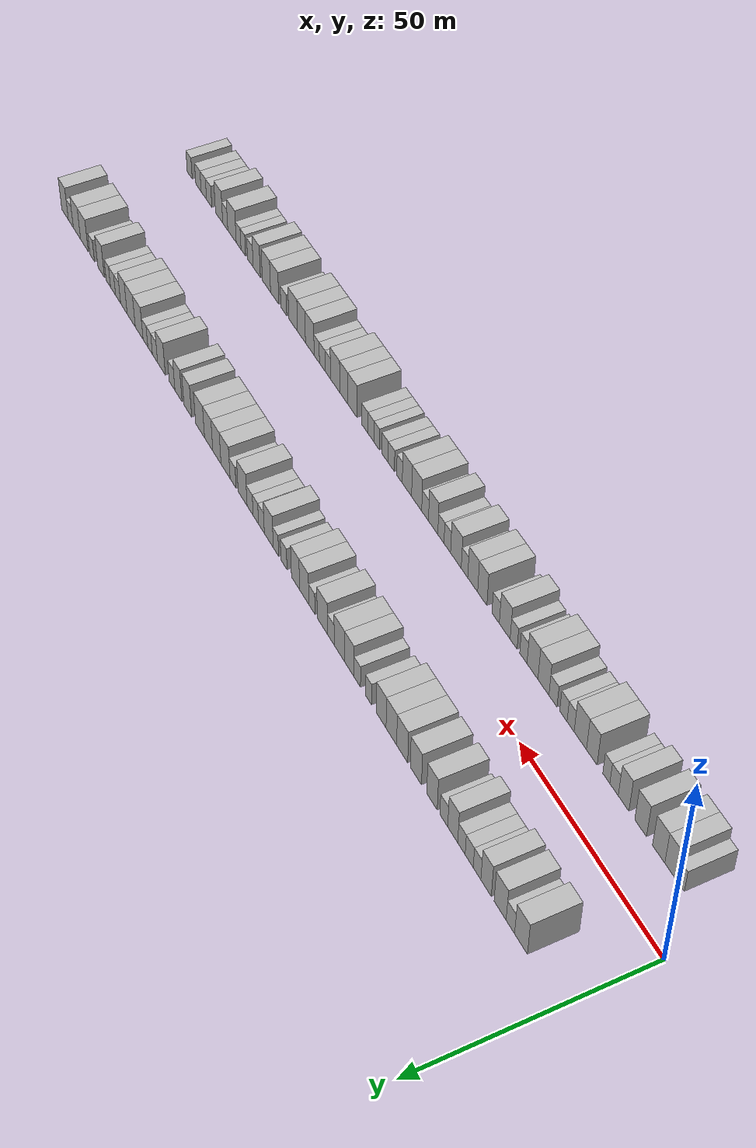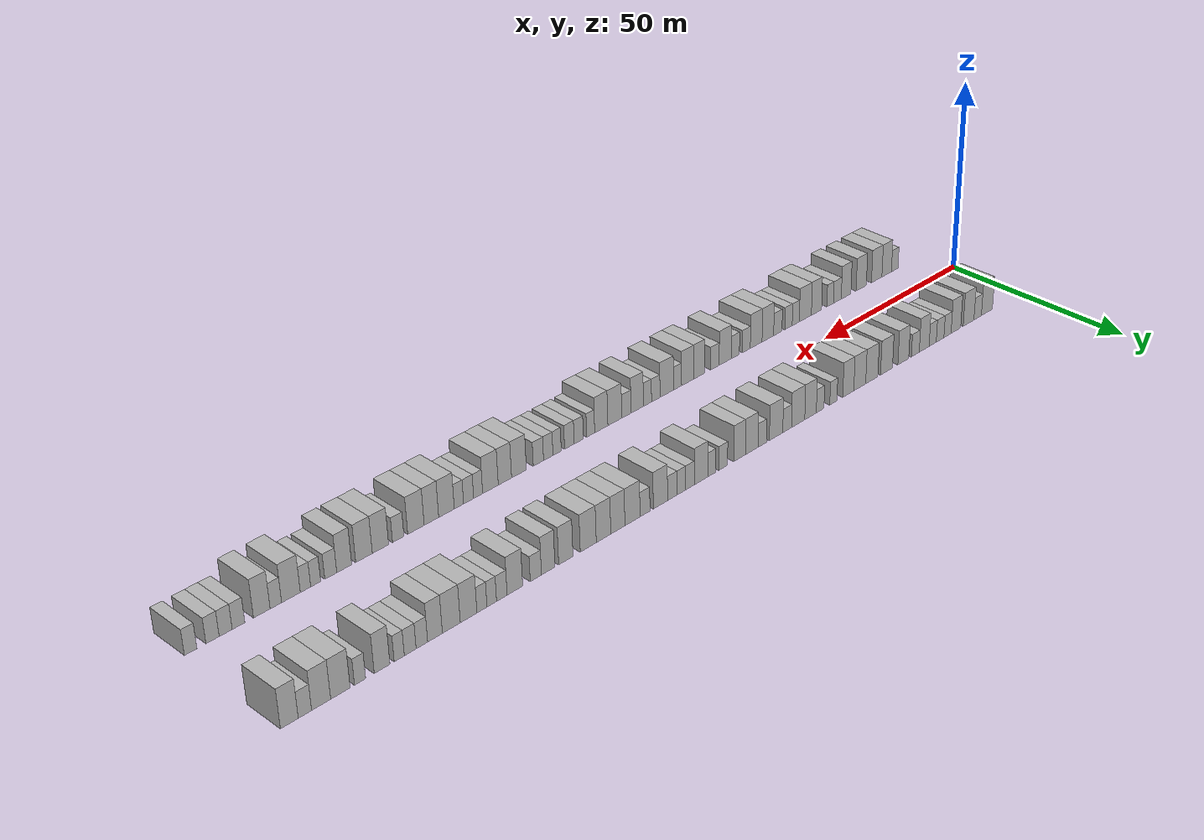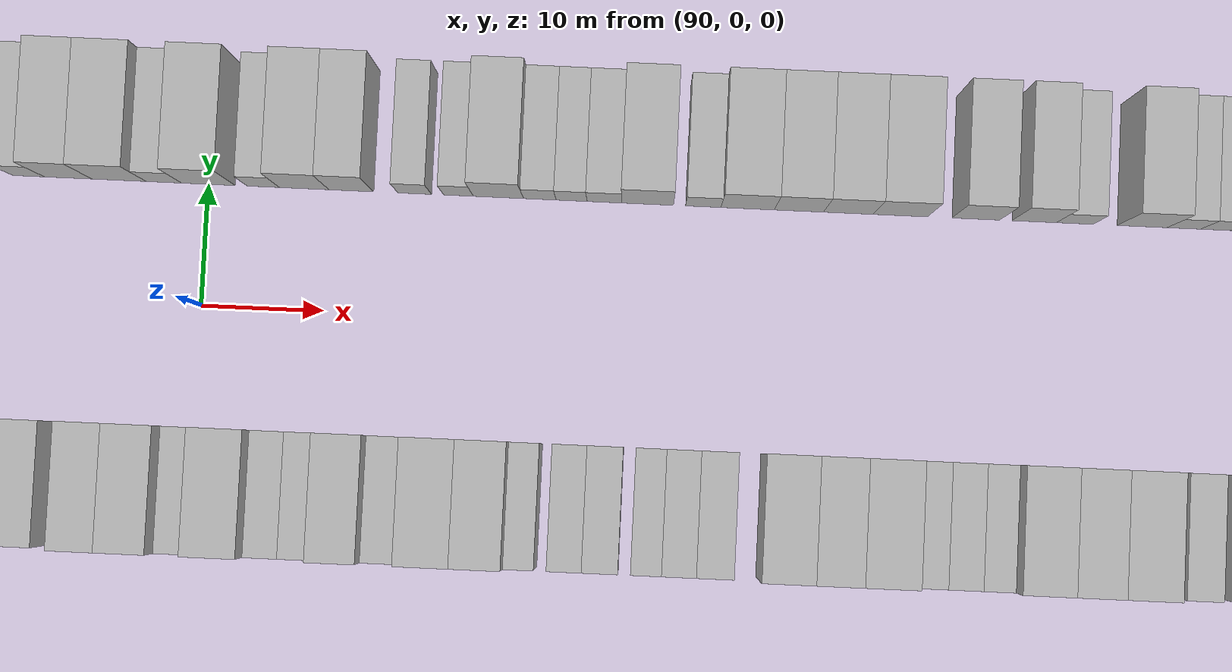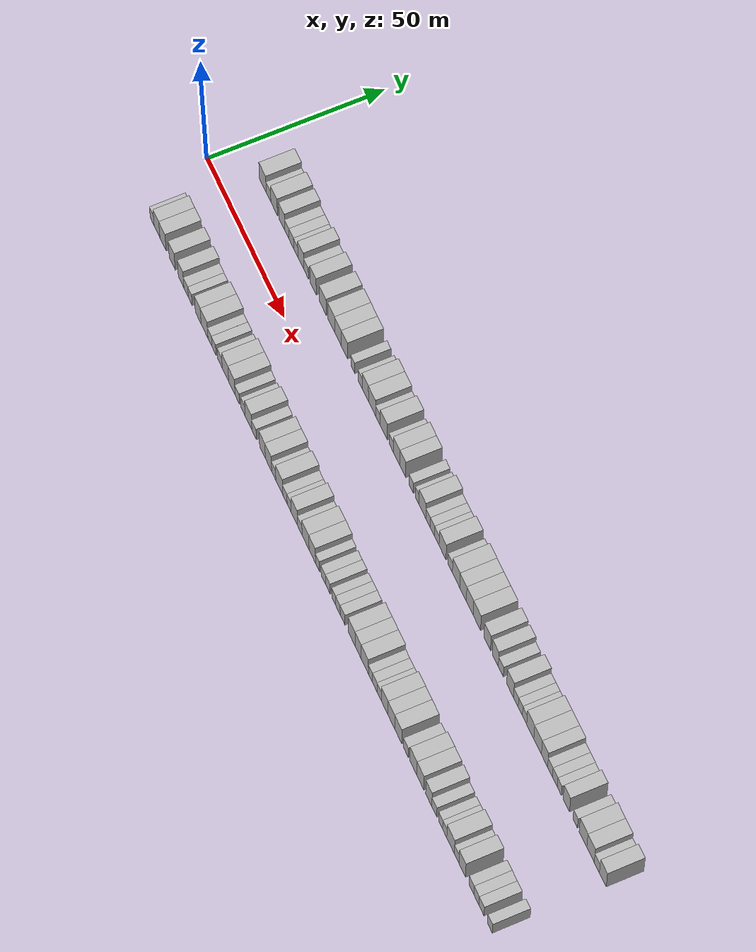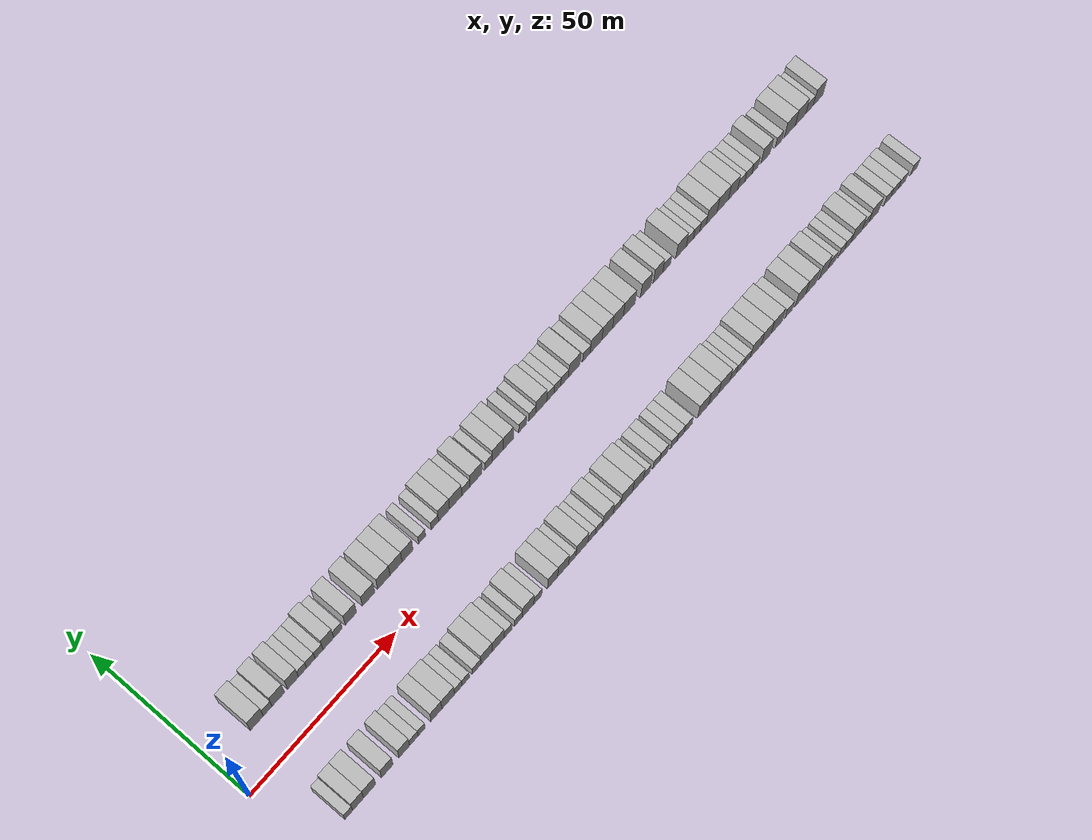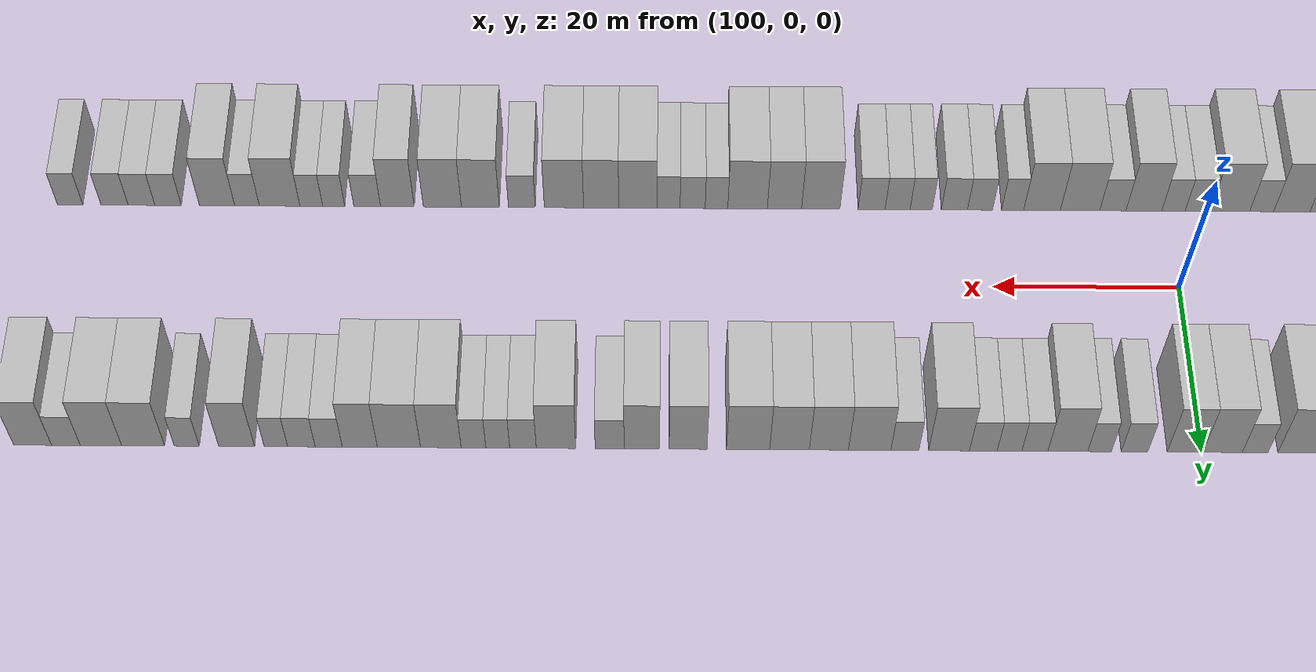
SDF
<sdf version="1.6">
 <world name="default">
  <scene>
   <sky><clouds><speed>12</speed></clouds></sky>
   <ambient>0.4 0.4 0.4 1</ambient>
   <background>0.7 0.7 0.7 1</background>
   <shadows>1</shadows>
  </scene>
  <gravity>0 0 -9.8066</gravity>
  <magnetic_field>6e-06 2.3e-05 -4.2e-05</magnetic_field>
  <physics default="0" name="default_physics" type="ode">
   <ode>
    <solver>
     <type>quick</type>
     <iters>10</iters>
     <sor>1.0</sor>
     <use_dynamic_moi_rescaling>0</use_dynamic_moi_rescaling>
    </solver>
    <constraints>
     <cfm>0</cfm>
     <erp>0.2</erp>
     <contact_max_correcting_vel>100</contact_max_correcting_vel>
     <contact_surface_layer>0.001</contact_surface_layer>
    </constraints>
   </ode>
   <max_step_size>0.004</max_step_size>
   <real_time_factor>1</real_time_factor>
   <real_time_update_rate>250</real_time_update_rate>
  </physics>
  <light name="sun" type="directional">
   <pose>0 0 10 0 0 0</pose>
   <diffuse>0.8 0.8 0.8 1</diffuse>
   <specular>0.2 0.2 0.2 1</specular>
   <attenuation>
    <range>1000</range>
    <constant>0.9</constant>
    <linear>0.01</linear>
    <quadratic>0.001</quadratic>
   </attenuation>
   <direction>-0.5 0.1 -0.9</direction>
  </light>
  <model name="building_1">
   <static>1</static>
   <pose>13.2188 15.0000 0 0.000000 0.000000 1.570796</pose>
   <link name="link">
    <pose>0 0 4.50 0 0 0</pose>
    <collision name="collision"><geometry><box><size>10.0000 4.4376 9.0000</size></box></geometry></collision>
    <visual name="visual">
     <cast_shadows>0</cast_shadows>
     <geometry><box><size>10.0000 4.4376 9.0000</size></box></geometry>
     <material>
      <script>
       <uri>model://HANNAS_wall/materials/scripts</uri>
       <uri>model://HANNAS_wall/materials/textures</uri>
       <name>vrc/HANNAS_wall</name>
      </script>
     </material>
    </visual>
   </link>
  </model>
  <model name="building_2">
   <static>1</static>
   <pose>16.9260 15.0000 0 0.000000 0.000000 1.570796</pose>
   <link name="link">
    <pose>0 0 3.00 0 0 0</pose>
    <collision name="collision"><geometry><box><size>10.0000 2.9768 6.0000</size></box></geometry></collision>
    <visual name="visual">
     <cast_shadows>0</cast_shadows>
     <geometry><box><size>10.0000 2.9768 6.0000</size></box></geometry>
     <material>
      <script>
       <uri>model://HANNAS_wall/materials/scripts</uri>
       <uri>model://HANNAS_wall/materials/textures</uri>
       <name>vrc/HANNAS_wall</name>
      </script>
     </material>
    </visual>
   </link>
  </model>
  <model name="building_3">
   <static>1</static>
   <pose>20.5367 15.0000 0 0.000000 0.000000 1.570796</pose>
   <link name="link">
    <pose>0 0 4.50 0 0 0</pose>
    <collision name="collision"><geometry><box><size>10.0000 4.2446 9.0000</size></box></geometry></collision>
    <visual name="visual">
     <cast_shadows>0</cast_shadows>
     <geometry><box><size>10.0000 4.2446 9.0000</size></box></geometry>
     <material>
      <script>
       <uri>model://HANNAS_wall/materials/scripts</uri>
       <uri>model://HANNAS_wall/materials/textures</uri>
       <name>vrc/HANNAS_wall</name>
      </script>
     </material>
    </visual>
   </link>
  </model>
  <model name="building_4">
   <static>1</static>
   <pose>25.5316 15.0000 0 0.000000 0.000000 1.570796</pose>
   <link name="link">
    <pose>0 0 4.50 0 0 0</pose>
    <collision name="collision"><geometry><box><size>10.0000 3.7453 9.0000</size></box></geometry></collision>
    <visual name="visual">
     <cast_shadows>0</cast_shadows>
     <geometry><box><size>10.0000 3.7453 9.0000</size></box></geometry>
     <material>
      <script>
       <uri>model://HANNAS_wall/materials/scripts</uri>
       <uri>model://HANNAS_wall/materials/textures</uri>
       <name>vrc/HANNAS_wall</name>
      </script>
     </material>
    </visual>
   </link>
  </model>
  <model name="building_5">
   <static>1</static>
   <pose>28.7888 15.0000 0 0.000000 0.000000 1.570796</pose>
   <link name="link">
    <pose>0 0 3.00 0 0 0</pose>
    <collision name="collision"><geometry><box><size>10.0000 2.7692 6.0000</size></box></geometry></collision>
    <visual name="visual">
     <cast_shadows>0</cast_shadows>
     <geometry><box><size>10.0000 2.7692 6.0000</size></box></geometry>
     <material>
      <script>
       <uri>model://HANNAS_wall/materials/scripts</uri>
       <uri>model://HANNAS_wall/materials/textures</uri>
       <name>vrc/HANNAS_wall</name>
      </script>
     </material>
    </visual>
   </link>
  </model>
  <model name="building_6">
   <static>1</static>
   <pose>31.6491 15.0000 0 0.000000 0.000000 1.570796</pose>
   <link name="link">
    <pose>0 0 3.00 0 0 0</pose>
    <collision name="collision"><geometry><box><size>10.0000 2.9513 6.0000</size></box></geometry></collision>
    <visual name="visual">
     <cast_shadows>0</cast_shadows>
     <geometry><box><size>10.0000 2.9513 6.0000</size></box></geometry>
     <material>
      <script>
       <uri>model://HANNAS_wall/materials/scripts</uri>
       <uri>model://HANNAS_wall/materials/textures</uri>
       <name>vrc/HANNAS_wall</name>
      </script>
     </material>
    </visual>
   </link>
  </model>
  <model name="building_7">
   <static>1</static>
   <pose>34.4945 15.0000 0 0.000000 0.000000 1.570796</pose>
   <link name="link">
    <pose>0 0 3.00 0 0 0</pose>
    <collision name="collision"><geometry><box><size>10.0000 2.7396 6.0000</size></box></geometry></collision>
    <visual name="visual">
     <cast_shadows>0</cast_shadows>
     <geometry><box><size>10.0000 2.7396 6.0000</size></box></geometry>
     <material>
      <script>
       <uri>model://HANNAS_wall/materials/scripts</uri>
       <uri>model://HANNAS_wall/materials/textures</uri>
       <name>vrc/HANNAS_wall</name>
      </script>
     </material>
    </visual>
   </link>
  </model>
  <model name="building_8">
   <static>1</static>
   <pose>37.7245 15.0000 0 0.000000 0.000000 1.570796</pose>
   <link name="link">
    <pose>0 0 4.50 0 0 0</pose>
    <collision name="collision"><geometry><box><size>10.0000 3.7204 9.0000</size></box></geometry></collision>
    <visual name="visual">
     <cast_shadows>0</cast_shadows>
     <geometry><box><size>10.0000 3.7204 9.0000</size></box></geometry>
     <material>
      <script>
       <uri>model://HANNAS_wall/materials/scripts</uri>
       <uri>model://HANNAS_wall/materials/textures</uri>
       <name>vrc/HANNAS_wall</name>
      </script>
     </material>
    </visual>
   </link>
  </model>
  <model name="building_9">
   <static>1</static>
   <pose>41.0655 15.0000 0 0.000000 0.000000 1.570796</pose>
   <link name="link">
    <pose>0 0 3.00 0 0 0</pose>
    <collision name="collision"><geometry><box><size>10.0000 2.9615 6.0000</size></box></geometry></collision>
    <visual name="visual">
     <cast_shadows>0</cast_shadows>
     <geometry><box><size>10.0000 2.9615 6.0000</size></box></geometry>
     <material>
      <script>
       <uri>model://HANNAS_wall/materials/scripts</uri>
       <uri>model://HANNAS_wall/materials/textures</uri>
       <name>vrc/HANNAS_wall</name>
      </script>
     </material>
    </visual>
   </link>
  </model>
  <model name="building_10">
   <static>1</static>
   <pose>45.5478 15.0000 0 0.000000 0.000000 1.570796</pose>
   <link name="link">
    <pose>0 0 4.50 0 0 0</pose>
    <collision name="collision"><geometry><box><size>10.0000 4.0031 9.0000</size></box></geometry></collision>
    <visual name="visual">
     <cast_shadows>0</cast_shadows>
     <geometry><box><size>10.0000 4.0031 9.0000</size></box></geometry>
     <material>
      <script>
       <uri>model://HANNAS_wall/materials/scripts</uri>
       <uri>model://HANNAS_wall/materials/textures</uri>
       <name>vrc/HANNAS_wall</name>
      </script>
     </material>
    </visual>
   </link>
  </model>
  <model name="building_11">
   <static>1</static>
   <pose>51.7211 15.0000 0 0.000000 0.000000 1.570796</pose>
   <link name="link">
    <pose>0 0 4.50 0 0 0</pose>
    <collision name="collision"><geometry><box><size>10.0000 4.3435 9.0000</size></box></geometry></collision>
    <visual name="visual">
     <cast_shadows>0</cast_shadows>
     <geometry><box><size>10.0000 4.3435 9.0000</size></box></geometry>
     <material>
      <script>
       <uri>model://HANNAS_wall/materials/scripts</uri>
       <uri>model://HANNAS_wall/materials/textures</uri>
       <name>vrc/HANNAS_wall</name>
      </script>
     </material>
    </visual>
   </link>
  </model>
  <model name="building_12">
   <static>1</static>
   <pose>57.0680 15.0000 0 0.000000 0.000000 1.570796</pose>
   <link name="link">
    <pose>0 0 4.50 0 0 0</pose>
    <collision name="collision"><geometry><box><size>10.0000 4.3503 9.0000</size></box></geometry></collision>
    <visual name="visual">
     <cast_shadows>0</cast_shadows>
     <geometry><box><size>10.0000 4.3503 9.0000</size></box></geometry>
     <material>
      <script>
       <uri>model://HANNAS_wall/materials/scripts</uri>
       <uri>model://HANNAS_wall/materials/textures</uri>
       <name>vrc/HANNAS_wall</name>
      </script>
     </material>
    </visual>
   </link>
  </model>
  <model name="building_13">
   <static>1</static>
   <pose>61.3553 15.0000 0 0.000000 0.000000 1.570796</pose>
   <link name="link">
    <pose>0 0 4.50 0 0 0</pose>
    <collision name="collision"><geometry><box><size>10.0000 4.2243 9.0000</size></box></geometry></collision>
    <visual name="visual">
     <cast_shadows>0</cast_shadows>
     <geometry><box><size>10.0000 4.2243 9.0000</size></box></geometry>
     <material>
      <script>
       <uri>model://HANNAS_wall/materials/scripts</uri>
       <uri>model://HANNAS_wall/materials/textures</uri>
       <name>vrc/HANNAS_wall</name>
      </script>
     </material>
    </visual>
   </link>
  </model>
  <model name="building_14">
   <static>1</static>
   <pose>65.4110 15.0000 0 0.000000 0.000000 1.570796</pose>
   <link name="link">
    <pose>0 0 4.50 0 0 0</pose>
    <collision name="collision"><geometry><box><size>10.0000 3.8870 9.0000</size></box></geometry></collision>
    <visual name="visual">
     <cast_shadows>0</cast_shadows>
     <geometry><box><size>10.0000 3.8870 9.0000</size></box></geometry>
     <material>
      <script>
       <uri>model://HANNAS_wall/materials/scripts</uri>
       <uri>model://HANNAS_wall/materials/textures</uri>
       <name>vrc/HANNAS_wall</name>
      </script>
     </material>
    </visual>
   </link>
  </model>
  <model name="building_15">
   <static>1</static>
   <pose>70.6132 15.0000 0 0.000000 0.000000 1.570796</pose>
   <link name="link">
    <pose>0 0 3.00 0 0 0</pose>
    <collision name="collision"><geometry><box><size>10.0000 2.5174 6.0000</size></box></geometry></collision>
    <visual name="visual">
     <cast_shadows>0</cast_shadows>
     <geometry><box><size>10.0000 2.5174 6.0000</size></box></geometry>
     <material>
      <script>
       <uri>model://HANNAS_wall/materials/scripts</uri>
       <uri>model://HANNAS_wall/materials/textures</uri>
       <name>vrc/HANNAS_wall</name>
      </script>
     </material>
    </visual>
   </link>
  </model>
  <model name="building_16">
   <static>1</static>
   <pose>75.1780 15.0000 0 0.000000 0.000000 1.570796</pose>
   <link name="link">
    <pose>0 0 3.00 0 0 0</pose>
    <collision name="collision"><geometry><box><size>10.0000 2.6121 6.0000</size></box></geometry></collision>
    <visual name="visual">
     <cast_shadows>0</cast_shadows>
     <geometry><box><size>10.0000 2.6121 6.0000</size></box></geometry>
     <material>
      <script>
       <uri>model://HANNAS_wall/materials/scripts</uri>
       <uri>model://HANNAS_wall/materials/textures</uri>
       <name>vrc/HANNAS_wall</name>
      </script>
     </material>
    </visual>
   </link>
  </model>
  <model name="building_17">
   <static>1</static>
   <pose>78.4476 15.0000 0 0.000000 0.000000 1.570796</pose>
   <link name="link">
    <pose>0 0 4.50 0 0 0</pose>
    <collision name="collision"><geometry><box><size>10.0000 3.9272 9.0000</size></box></geometry></collision>
    <visual name="visual">
     <cast_shadows>0</cast_shadows>
     <geometry><box><size>10.0000 3.9272 9.0000</size></box></geometry>
     <material>
      <script>
       <uri>model://HANNAS_wall/materials/scripts</uri>
       <uri>model://HANNAS_wall/materials/textures</uri>
       <name>vrc/HANNAS_wall</name>
      </script>
     </material>
    </visual>
   </link>
  </model>
  <model name="building_18">
   <static>1</static>
   <pose>82.6273 15.0000 0 0.000000 0.000000 1.570796</pose>
   <link name="link">
    <pose>0 0 4.50 0 0 0</pose>
    <collision name="collision"><geometry><box><size>10.0000 4.4322 9.0000</size></box></geometry></collision>
    <visual name="visual">
     <cast_shadows>0</cast_shadows>
     <geometry><box><size>10.0000 4.4322 9.0000</size></box></geometry>
     <material>
      <script>
       <uri>model://HANNAS_wall/materials/scripts</uri>
       <uri>model://HANNAS_wall/materials/textures</uri>
       <name>vrc/HANNAS_wall</name>
      </script>
     </material>
    </visual>
   </link>
  </model>
  <model name="building_19">
   <static>1</static>
   <pose>86.2931 15.0000 0 0.000000 0.000000 1.570796</pose>
   <link name="link">
    <pose>0 0 3.00 0 0 0</pose>
    <collision name="collision"><geometry><box><size>10.0000 2.8995 6.0000</size></box></geometry></collision>
    <visual name="visual">
     <cast_shadows>0</cast_shadows>
     <geometry><box><size>10.0000 2.8995 6.0000</size></box></geometry>
     <material>
      <script>
       <uri>model://HANNAS_wall/materials/scripts</uri>
       <uri>model://HANNAS_wall/materials/textures</uri>
       <name>vrc/HANNAS_wall</name>
      </script>
     </material>
    </visual>
   </link>
  </model>
  <model name="building_20">
   <static>1</static>
   <pose>89.9431 15.0000 0 0.000000 0.000000 1.570796</pose>
   <link name="link">
    <pose>0 0 4.50 0 0 0</pose>
    <collision name="collision"><geometry><box><size>10.0000 4.4005 9.0000</size></box></geometry></collision>
    <visual name="visual">
     <cast_shadows>0</cast_shadows>
     <geometry><box><size>10.0000 4.4005 9.0000</size></box></geometry>
     <material>
      <script>
       <uri>model://HANNAS_wall/materials/scripts</uri>
       <uri>model://HANNAS_wall/materials/textures</uri>
       <name>vrc/HANNAS_wall</name>
      </script>
     </material>
    </visual>
   </link>
  </model>
  <model name="building_21">
   <static>1</static>
   <pose>94.4690 15.0000 0 0.000000 0.000000 1.570796</pose>
   <link name="link">
    <pose>0 0 3.00 0 0 0</pose>
    <collision name="collision"><geometry><box><size>10.0000 2.6513 6.0000</size></box></geometry></collision>
    <visual name="visual">
     <cast_shadows>0</cast_shadows>
     <geometry><box><size>10.0000 2.6513 6.0000</size></box></geometry>
     <material>
      <script>
       <uri>model://HANNAS_wall/materials/scripts</uri>
       <uri>model://HANNAS_wall/materials/textures</uri>
       <name>vrc/HANNAS_wall</name>
      </script>
     </material>
    </visual>
   </link>
  </model>
  <model name="building_22">
   <static>1</static>
   <pose>97.8308 15.0000 0 0.000000 0.000000 1.570796</pose>
   <link name="link">
    <pose>0 0 4.50 0 0 0</pose>
    <collision name="collision"><geometry><box><size>10.0000 4.0723 9.0000</size></box></geometry></collision>
    <visual name="visual">
     <cast_shadows>0</cast_shadows>
     <geometry><box><size>10.0000 4.0723 9.0000</size></box></geometry>
     <material>
      <script>
       <uri>model://HANNAS_wall/materials/scripts</uri>
       <uri>model://HANNAS_wall/materials/textures</uri>
       <name>vrc/HANNAS_wall</name>
      </script>
     </material>
    </visual>
   </link>
  </model>
  <model name="building_23">
   <static>1</static>
   <pose>101.7011 15.0000 0 0.000000 0.000000 1.570796</pose>
   <link name="link">
    <pose>0 0 4.50 0 0 0</pose>
    <collision name="collision"><geometry><box><size>10.0000 3.6684 9.0000</size></box></geometry></collision>
    <visual name="visual">
     <cast_shadows>0</cast_shadows>
     <geometry><box><size>10.0000 3.6684 9.0000</size></box></geometry>
     <material>
      <script>
       <uri>model://HANNAS_wall/materials/scripts</uri>
       <uri>model://HANNAS_wall/materials/textures</uri>
       <name>vrc/HANNAS_wall</name>
      </script>
     </material>
    </visual>
   </link>
  </model>
  <model name="building_24">
   <static>1</static>
   <pose>106.9101 15.0000 0 0.000000 0.000000 1.570796</pose>
   <link name="link">
    <pose>0 0 3.00 0 0 0</pose>
    <collision name="collision"><geometry><box><size>10.0000 2.7494 6.0000</size></box></geometry></collision>
    <visual name="visual">
     <cast_shadows>0</cast_shadows>
     <geometry><box><size>10.0000 2.7494 6.0000</size></box></geometry>
     <material>
      <script>
       <uri>model://HANNAS_wall/materials/scripts</uri>
       <uri>model://HANNAS_wall/materials/textures</uri>
       <name>vrc/HANNAS_wall</name>
      </script>
     </material>
    </visual>
   </link>
  </model>
  <model name="building_25">
   <static>1</static>
   <pose>110.5071 15.0000 0 0.000000 0.000000 1.570796</pose>
   <link name="link">
    <pose>0 0 3.00 0 0 0</pose>
    <collision name="collision"><geometry><box><size>10.0000 2.4445 6.0000</size></box></geometry></collision>
    <visual name="visual">
     <cast_shadows>0</cast_shadows>
     <geometry><box><size>10.0000 2.4445 6.0000</size></box></geometry>
     <material>
      <script>
       <uri>model://HANNAS_wall/materials/scripts</uri>
       <uri>model://HANNAS_wall/materials/textures</uri>
       <name>vrc/HANNAS_wall</name>
      </script>
     </material>
    </visual>
   </link>
  </model>
  <model name="building_26">
   <static>1</static>
   <pose>113.7879 15.0000 0 0.000000 0.000000 1.570796</pose>
   <link name="link">
    <pose>0 0 4.50 0 0 0</pose>
    <collision name="collision"><geometry><box><size>10.0000 4.1172 9.0000</size></box></geometry></collision>
    <visual name="visual">
     <cast_shadows>0</cast_shadows>
     <geometry><box><size>10.0000 4.1172 9.0000</size></box></geometry>
     <material>
      <script>
       <uri>model://HANNAS_wall/materials/scripts</uri>
       <uri>model://HANNAS_wall/materials/textures</uri>
       <name>vrc/HANNAS_wall</name>
      </script>
     </material>
    </visual>
   </link>
  </model>
  <model name="building_27">
   <static>1</static>
   <pose>117.1877 15.0000 0 0.000000 0.000000 1.570796</pose>
   <link name="link">
    <pose>0 0 3.00 0 0 0</pose>
    <collision name="collision"><geometry><box><size>10.0000 2.6824 6.0000</size></box></geometry></collision>
    <visual name="visual">
     <cast_shadows>0</cast_shadows>
     <geometry><box><size>10.0000 2.6824 6.0000</size></box></geometry>
     <material>
      <script>
       <uri>model://HANNAS_wall/materials/scripts</uri>
       <uri>model://HANNAS_wall/materials/textures</uri>
       <name>vrc/HANNAS_wall</name>
      </script>
     </material>
    </visual>
   </link>
  </model>
  <model name="building_28">
   <static>1</static>
   <pose>119.7982 15.0000 0 0.000000 0.000000 1.570796</pose>
   <link name="link">
    <pose>0 0 3.00 0 0 0</pose>
    <collision name="collision"><geometry><box><size>10.0000 2.5385 6.0000</size></box></geometry></collision>
    <visual name="visual">
     <cast_shadows>0</cast_shadows>
     <geometry><box><size>10.0000 2.5385 6.0000</size></box></geometry>
     <material>
      <script>
       <uri>model://HANNAS_wall/materials/scripts</uri>
       <uri>model://HANNAS_wall/materials/textures</uri>
       <name>vrc/HANNAS_wall</name>
      </script>
     </material>
    </visual>
   </link>
  </model>
  <model name="building_29">
   <static>1</static>
   <pose>122.4933 15.0000 0 0.000000 0.000000 1.570796</pose>
   <link name="link">
    <pose>0 0 3.00 0 0 0</pose>
    <collision name="collision"><geometry><box><size>10.0000 2.8517 6.0000</size></box></geometry></collision>
    <visual name="visual">
     <cast_shadows>0</cast_shadows>
     <geometry><box><size>10.0000 2.8517 6.0000</size></box></geometry>
     <material>
      <script>
       <uri>model://HANNAS_wall/materials/scripts</uri>
       <uri>model://HANNAS_wall/materials/textures</uri>
       <name>vrc/HANNAS_wall</name>
      </script>
     </material>
    </visual>
   </link>
  </model>
  <model name="building_30">
   <static>1</static>
   <pose>126.0310 15.0000 0 0.000000 0.000000 1.570796</pose>
   <link name="link">
    <pose>0 0 4.50 0 0 0</pose>
    <collision name="collision"><geometry><box><size>10.0000 4.2237 9.0000</size></box></geometry></collision>
    <visual name="visual">
     <cast_shadows>0</cast_shadows>
     <geometry><box><size>10.0000 4.2237 9.0000</size></box></geometry>
     <material>
      <script>
       <uri>model://HANNAS_wall/materials/scripts</uri>
       <uri>model://HANNAS_wall/materials/textures</uri>
       <name>vrc/HANNAS_wall</name>
      </script>
     </material>
    </visual>
   </link>
  </model>
  <model name="building_31">
   <static>1</static>
   <pose>130.5884 15.0000 0 0.000000 0.000000 1.570796</pose>
   <link name="link">
    <pose>0 0 3.00 0 0 0</pose>
    <collision name="collision"><geometry><box><size>10.0000 2.8909 6.0000</size></box></geometry></collision>
    <visual name="visual">
     <cast_shadows>0</cast_shadows>
     <geometry><box><size>10.0000 2.8909 6.0000</size></box></geometry>
     <material>
      <script>
       <uri>model://HANNAS_wall/materials/scripts</uri>
       <uri>model://HANNAS_wall/materials/textures</uri>
       <name>vrc/HANNAS_wall</name>
      </script>
     </material>
    </visual>
   </link>
  </model>
  <model name="building_32">
   <static>1</static>
   <pose>134.2233 15.0000 0 0.000000 0.000000 1.570796</pose>
   <link name="link">
    <pose>0 0 4.50 0 0 0</pose>
    <collision name="collision"><geometry><box><size>10.0000 4.3790 9.0000</size></box></geometry></collision>
    <visual name="visual">
     <cast_shadows>0</cast_shadows>
     <geometry><box><size>10.0000 4.3790 9.0000</size></box></geometry>
     <material>
      <script>
       <uri>model://HANNAS_wall/materials/scripts</uri>
       <uri>model://HANNAS_wall/materials/textures</uri>
       <name>vrc/HANNAS_wall</name>
      </script>
     </material>
    </visual>
   </link>
  </model>
  <model name="building_33">
   <static>1</static>
   <pose>138.4308 15.0000 0 0.000000 0.000000 1.570796</pose>
   <link name="link">
    <pose>0 0 4.50 0 0 0</pose>
    <collision name="collision"><geometry><box><size>10.0000 4.0360 9.0000</size></box></geometry></collision>
    <visual name="visual">
     <cast_shadows>0</cast_shadows>
     <geometry><box><size>10.0000 4.0360 9.0000</size></box></geometry>
     <material>
      <script>
       <uri>model://HANNAS_wall/materials/scripts</uri>
       <uri>model://HANNAS_wall/materials/textures</uri>
       <name>vrc/HANNAS_wall</name>
      </script>
     </material>
    </visual>
   </link>
  </model>
  <model name="building_34">
   <static>1</static>
   <pose>142.4952 15.0000 0 0.000000 0.000000 1.570796</pose>
   <link name="link">
    <pose>0 0 4.50 0 0 0</pose>
    <collision name="collision"><geometry><box><size>10.0000 4.0927 9.0000</size></box></geometry></collision>
    <visual name="visual">
     <cast_shadows>0</cast_shadows>
     <geometry><box><size>10.0000 4.0927 9.0000</size></box></geometry>
     <material>
      <script>
       <uri>model://HANNAS_wall/materials/scripts</uri>
       <uri>model://HANNAS_wall/materials/textures</uri>
       <name>vrc/HANNAS_wall</name>
      </script>
     </material>
    </visual>
   </link>
  </model>
  <model name="building_35">
   <static>1</static>
   <pose>146.7730 15.0000 0 0.000000 0.000000 1.570796</pose>
   <link name="link">
    <pose>0 0 4.50 0 0 0</pose>
    <collision name="collision"><geometry><box><size>10.0000 4.4629 9.0000</size></box></geometry></collision>
    <visual name="visual">
     <cast_shadows>0</cast_shadows>
     <geometry><box><size>10.0000 4.4629 9.0000</size></box></geometry>
     <material>
      <script>
       <uri>model://HANNAS_wall/materials/scripts</uri>
       <uri>model://HANNAS_wall/materials/textures</uri>
       <name>vrc/HANNAS_wall</name>
      </script>
     </material>
    </visual>
   </link>
  </model>
  <model name="building_36">
   <static>1</static>
   <pose>152.9612 15.0000 0 0.000000 0.000000 1.570796</pose>
   <link name="link">
    <pose>0 0 4.50 0 0 0</pose>
    <collision name="collision"><geometry><box><size>10.0000 3.9135 9.0000</size></box></geometry></collision>
    <visual name="visual">
     <cast_shadows>0</cast_shadows>
     <geometry><box><size>10.0000 3.9135 9.0000</size></box></geometry>
     <material>
      <script>
       <uri>model://HANNAS_wall/materials/scripts</uri>
       <uri>model://HANNAS_wall/materials/textures</uri>
       <name>vrc/HANNAS_wall</name>
      </script>
     </material>
    </visual>
   </link>
  </model>
  <model name="building_37">
   <static>1</static>
   <pose>157.7371 15.0000 0 0.000000 0.000000 1.570796</pose>
   <link name="link">
    <pose>0 0 4.50 0 0 0</pose>
    <collision name="collision"><geometry><box><size>10.0000 3.6383 9.0000</size></box></geometry></collision>
    <visual name="visual">
     <cast_shadows>0</cast_shadows>
     <geometry><box><size>10.0000 3.6383 9.0000</size></box></geometry>
     <material>
      <script>
       <uri>model://HANNAS_wall/materials/scripts</uri>
       <uri>model://HANNAS_wall/materials/textures</uri>
       <name>vrc/HANNAS_wall</name>
      </script>
     </material>
    </visual>
   </link>
  </model>
  <model name="building_38">
   <static>1</static>
   <pose>161.0521 15.0000 0 0.000000 0.000000 1.570796</pose>
   <link name="link">
    <pose>0 0 3.00 0 0 0</pose>
    <collision name="collision"><geometry><box><size>10.0000 2.9917 6.0000</size></box></geometry></collision>
    <visual name="visual">
     <cast_shadows>0</cast_shadows>
     <geometry><box><size>10.0000 2.9917 6.0000</size></box></geometry>
     <material>
      <script>
       <uri>model://HANNAS_wall/materials/scripts</uri>
       <uri>model://HANNAS_wall/materials/textures</uri>
       <name>vrc/HANNAS_wall</name>
      </script>
     </material>
    </visual>
   </link>
  </model>
  <model name="building_39">
   <static>1</static>
   <pose>166.5863 15.0000 0 0.000000 0.000000 1.570796</pose>
   <link name="link">
    <pose>0 0 4.50 0 0 0</pose>
    <collision name="collision"><geometry><box><size>10.0000 4.0768 9.0000</size></box></geometry></collision>
    <visual name="visual">
     <cast_shadows>0</cast_shadows>
     <geometry><box><size>10.0000 4.0768 9.0000</size></box></geometry>
     <material>
      <script>
       <uri>model://HANNAS_wall/materials/scripts</uri>
       <uri>model://HANNAS_wall/materials/textures</uri>
       <name>vrc/HANNAS_wall</name>
      </script>
     </material>
    </visual>
   </link>
  </model>
  <model name="building_40">
   <static>1</static>
   <pose>169.9971 15.0000 0 0.000000 0.000000 1.570796</pose>
   <link name="link">
    <pose>0 0 3.00 0 0 0</pose>
    <collision name="collision"><geometry><box><size>10.0000 2.7448 6.0000</size></box></geometry></collision>
    <visual name="visual">
     <cast_shadows>0</cast_shadows>
     <geometry><box><size>10.0000 2.7448 6.0000</size></box></geometry>
     <material>
      <script>
       <uri>model://HANNAS_wall/materials/scripts</uri>
       <uri>model://HANNAS_wall/materials/textures</uri>
       <name>vrc/HANNAS_wall</name>
      </script>
     </material>
    </visual>
   </link>
  </model>
  <model name="building_41">
   <static>1</static>
   <pose>172.5984 15.0000 0 0.000000 0.000000 1.570796</pose>
   <link name="link">
    <pose>0 0 3.00 0 0 0</pose>
    <collision name="collision"><geometry><box><size>10.0000 2.4578 6.0000</size></box></geometry></collision>
    <visual name="visual">
     <cast_shadows>0</cast_shadows>
     <geometry><box><size>10.0000 2.4578 6.0000</size></box></geometry>
     <material>
      <script>
       <uri>model://HANNAS_wall/materials/scripts</uri>
       <uri>model://HANNAS_wall/materials/textures</uri>
       <name>vrc/HANNAS_wall</name>
      </script>
     </material>
    </visual>
   </link>
  </model>
  <model name="building_42">
   <static>1</static>
   <pose>175.1026 15.0000 0 0.000000 0.000000 1.570796</pose>
   <link name="link">
    <pose>0 0 3.00 0 0 0</pose>
    <collision name="collision"><geometry><box><size>10.0000 2.5506 6.0000</size></box></geometry></collision>
    <visual name="visual">
     <cast_shadows>0</cast_shadows>
     <geometry><box><size>10.0000 2.5506 6.0000</size></box></geometry>
     <material>
      <script>
       <uri>model://HANNAS_wall/materials/scripts</uri>
       <uri>model://HANNAS_wall/materials/textures</uri>
       <name>vrc/HANNAS_wall</name>
      </script>
     </material>
    </visual>
   </link>
  </model>
  <model name="building_43">
   <static>1</static>
   <pose>178.4787 15.0000 0 0.000000 0.000000 1.570796</pose>
   <link name="link">
    <pose>0 0 4.50 0 0 0</pose>
    <collision name="collision"><geometry><box><size>10.0000 4.2018 9.0000</size></box></geometry></collision>
    <visual name="visual">
     <cast_shadows>0</cast_shadows>
     <geometry><box><size>10.0000 4.2018 9.0000</size></box></geometry>
     <material>
      <script>
       <uri>model://HANNAS_wall/materials/scripts</uri>
       <uri>model://HANNAS_wall/materials/textures</uri>
       <name>vrc/HANNAS_wall</name>
      </script>
     </material>
    </visual>
   </link>
  </model>
  <model name="building_44">
   <static>1</static>
   <pose>182.8127 15.0000 0 0.000000 0.000000 1.570796</pose>
   <link name="link">
    <pose>0 0 4.50 0 0 0</pose>
    <collision name="collision"><geometry><box><size>10.0000 4.4660 9.0000</size></box></geometry></collision>
    <visual name="visual">
     <cast_shadows>0</cast_shadows>
     <geometry><box><size>10.0000 4.4660 9.0000</size></box></geometry>
     <material>
      <script>
       <uri>model://HANNAS_wall/materials/scripts</uri>
       <uri>model://HANNAS_wall/materials/textures</uri>
       <name>vrc/HANNAS_wall</name>
      </script>
     </material>
    </visual>
   </link>
  </model>
  <model name="building_45">
   <static>1</static>
   <pose>186.8530 15.0000 0 0.000000 0.000000 1.570796</pose>
   <link name="link">
    <pose>0 0 4.50 0 0 0</pose>
    <collision name="collision"><geometry><box><size>10.0000 3.6148 9.0000</size></box></geometry></collision>
    <visual name="visual">
     <cast_shadows>0</cast_shadows>
     <geometry><box><size>10.0000 3.6148 9.0000</size></box></geometry>
     <material>
      <script>
       <uri>model://HANNAS_wall/materials/scripts</uri>
       <uri>model://HANNAS_wall/materials/textures</uri>
       <name>vrc/HANNAS_wall</name>
      </script>
     </material>
    </visual>
   </link>
  </model>
  <model name="building_46">
   <static>1</static>
   <pose>190.0587 15.0000 0 0.000000 0.000000 1.570796</pose>
   <link name="link">
    <pose>0 0 3.00 0 0 0</pose>
    <collision name="collision"><geometry><box><size>10.0000 2.7965 6.0000</size></box></geometry></collision>
    <visual name="visual">
     <cast_shadows>0</cast_shadows>
     <geometry><box><size>10.0000 2.7965 6.0000</size></box></geometry>
     <material>
      <script>
       <uri>model://HANNAS_wall/materials/scripts</uri>
       <uri>model://HANNAS_wall/materials/textures</uri>
       <name>vrc/HANNAS_wall</name>
      </script>
     </material>
    </visual>
   </link>
  </model>
  <model name="building_47">
   <static>1</static>
   <pose>192.8791 15.0000 0 0.000000 0.000000 1.570796</pose>
   <link name="link">
    <pose>0 0 3.00 0 0 0</pose>
    <collision name="collision"><geometry><box><size>10.0000 2.8443 6.0000</size></box></geometry></collision>
    <visual name="visual">
     <cast_shadows>0</cast_shadows>
     <geometry><box><size>10.0000 2.8443 6.0000</size></box></geometry>
     <material>
      <script>
       <uri>model://HANNAS_wall/materials/scripts</uri>
       <uri>model://HANNAS_wall/materials/textures</uri>
       <name>vrc/HANNAS_wall</name>
      </script>
     </material>
    </visual>
   </link>
  </model>
  <model name="building_48">
   <static>1</static>
   <pose>195.5133 15.0000 0 0.000000 0.000000 1.570796</pose>
   <link name="link">
    <pose>0 0 3.00 0 0 0</pose>
    <collision name="collision"><geometry><box><size>10.0000 2.4240 6.0000</size></box></geometry></collision>
    <visual name="visual">
     <cast_shadows>0</cast_shadows>
     <geometry><box><size>10.0000 2.4240 6.0000</size></box></geometry>
     <material>
      <script>
       <uri>model://HANNAS_wall/materials/scripts</uri>
       <uri>model://HANNAS_wall/materials/textures</uri>
       <name>vrc/HANNAS_wall</name>
      </script>
     </material>
    </visual>
   </link>
  </model>
  <model name="building_49">
   <static>1</static>
   <pose>199.5779 15.0000 0 0.000000 0.000000 1.570796</pose>
   <link name="link">
    <pose>0 0 4.50 0 0 0</pose>
    <collision name="collision"><geometry><box><size>10.0000 3.7052 9.0000</size></box></geometry></collision>
    <visual name="visual">
     <cast_shadows>0</cast_shadows>
     <geometry><box><size>10.0000 3.7052 9.0000</size></box></geometry>
     <material>
      <script>
       <uri>model://HANNAS_wall/materials/scripts</uri>
       <uri>model://HANNAS_wall/materials/textures</uri>
       <name>vrc/HANNAS_wall</name>
      </script>
     </material>
    </visual>
   </link>
  </model>
  <model name="building_50">
   <static>1</static>
   <pose>204.7219 15.0000 0 0.000000 0.000000 1.570796</pose>
   <link name="link">
    <pose>0 0 3.00 0 0 0</pose>
    <collision name="collision"><geometry><box><size>10.0000 2.5828 6.0000</size></box></geometry></collision>
    <visual name="visual">
     <cast_shadows>0</cast_shadows>
     <geometry><box><size>10.0000 2.5828 6.0000</size></box></geometry>
     <material>
      <script>
       <uri>model://HANNAS_wall/materials/scripts</uri>
       <uri>model://HANNAS_wall/materials/textures</uri>
       <name>vrc/HANNAS_wall</name>
      </script>
     </material>
    </visual>
   </link>
  </model>
  <model name="building_51">
   <static>1</static>
   <pose>209.2341 15.0000 0 0.000000 0.000000 1.570796</pose>
   <link name="link">
    <pose>0 0 4.50 0 0 0</pose>
    <collision name="collision"><geometry><box><size>10.0000 4.4417 9.0000</size></box></geometry></collision>
    <visual name="visual">
     <cast_shadows>0</cast_shadows>
     <geometry><box><size>10.0000 4.4417 9.0000</size></box></geometry>
     <material>
      <script>
       <uri>model://HANNAS_wall/materials/scripts</uri>
       <uri>model://HANNAS_wall/materials/textures</uri>
       <name>vrc/HANNAS_wall</name>
      </script>
     </material>
    </visual>
   </link>
  </model>
  <model name="building_52">
   <static>1</static>
   <pose>213.5964 15.0000 0 0.000000 0.000000 1.570796</pose>
   <link name="link">
    <pose>0 0 4.50 0 0 0</pose>
    <collision name="collision"><geometry><box><size>10.0000 4.2829 9.0000</size></box></geometry></collision>
    <visual name="visual">
     <cast_shadows>0</cast_shadows>
     <geometry><box><size>10.0000 4.2829 9.0000</size></box></geometry>
     <material>
      <script>
       <uri>model://HANNAS_wall/materials/scripts</uri>
       <uri>model://HANNAS_wall/materials/textures</uri>
       <name>vrc/HANNAS_wall</name>
      </script>
     </material>
    </visual>
   </link>
  </model>
  <model name="building_53">
   <static>1</static>
   <pose>217.2213 15.0000 0 0.000000 0.000000 1.570796</pose>
   <link name="link">
    <pose>0 0 3.00 0 0 0</pose>
    <collision name="collision"><geometry><box><size>10.0000 2.9670 6.0000</size></box></geometry></collision>
    <visual name="visual">
     <cast_shadows>0</cast_shadows>
     <geometry><box><size>10.0000 2.9670 6.0000</size></box></geometry>
     <material>
      <script>
       <uri>model://HANNAS_wall/materials/scripts</uri>
       <uri>model://HANNAS_wall/materials/textures</uri>
       <name>vrc/HANNAS_wall</name>
      </script>
     </material>
    </visual>
   </link>
  </model>
  <model name="building_54">
   <static>1</static>
   <pose>220.6630 15.0000 0 0.000000 0.000000 1.570796</pose>
   <link name="link">
    <pose>0 0 4.50 0 0 0</pose>
    <collision name="collision"><geometry><box><size>10.0000 3.9164 9.0000</size></box></geometry></collision>
    <visual name="visual">
     <cast_shadows>0</cast_shadows>
     <geometry><box><size>10.0000 3.9164 9.0000</size></box></geometry>
     <material>
      <script>
       <uri>model://HANNAS_wall/materials/scripts</uri>
       <uri>model://HANNAS_wall/materials/textures</uri>
       <name>vrc/HANNAS_wall</name>
      </script>
     </material>
    </visual>
   </link>
  </model>
  <model name="building_55">
   <static>1</static>
   <pose>11.3183 -15.0000 0 0.000000 0.000000 1.570796</pose>
   <link name="link">
    <pose>0 0 3.00 0 0 0</pose>
    <collision name="collision"><geometry><box><size>10.0000 2.6366 6.0000</size></box></geometry></collision>
    <visual name="visual">
     <cast_shadows>0</cast_shadows>
     <geometry><box><size>10.0000 2.6366 6.0000</size></box></geometry>
     <material>
      <script>
       <uri>model://HANNAS_wall/materials/scripts</uri>
       <uri>model://HANNAS_wall/materials/textures</uri>
       <name>vrc/HANNAS_wall</name>
      </script>
     </material>
    </visual>
   </link>
  </model>
  <model name="building_56">
   <static>1</static>
   <pose>14.5231 -15.0000 0 0.000000 0.000000 1.570796</pose>
   <link name="link">
    <pose>0 0 4.50 0 0 0</pose>
    <collision name="collision"><geometry><box><size>10.0000 3.7730 9.0000</size></box></geometry></collision>
    <visual name="visual">
     <cast_shadows>0</cast_shadows>
     <geometry><box><size>10.0000 3.7730 9.0000</size></box></geometry>
     <material>
      <script>
       <uri>model://HANNAS_wall/materials/scripts</uri>
       <uri>model://HANNAS_wall/materials/textures</uri>
       <name>vrc/HANNAS_wall</name>
      </script>
     </material>
    </visual>
   </link>
  </model>
  <model name="building_57">
   <static>1</static>
   <pose>18.4563 -15.0000 0 0.000000 0.000000 1.570796</pose>
   <link name="link">
    <pose>0 0 4.50 0 0 0</pose>
    <collision name="collision"><geometry><box><size>10.0000 4.0935 9.0000</size></box></geometry></collision>
    <visual name="visual">
     <cast_shadows>0</cast_shadows>
     <geometry><box><size>10.0000 4.0935 9.0000</size></box></geometry>
     <material>
      <script>
       <uri>model://HANNAS_wall/materials/scripts</uri>
       <uri>model://HANNAS_wall/materials/textures</uri>
       <name>vrc/HANNAS_wall</name>
      </script>
     </material>
    </visual>
   </link>
  </model>
  <model name="building_58">
   <static>1</static>
   <pose>24.4875 -15.0000 0 0.000000 0.000000 1.570796</pose>
   <link name="link">
    <pose>0 0 4.50 0 0 0</pose>
    <collision name="collision"><geometry><box><size>10.0000 3.9688 9.0000</size></box></geometry></collision>
    <visual name="visual">
     <cast_shadows>0</cast_shadows>
     <geometry><box><size>10.0000 3.9688 9.0000</size></box></geometry>
     <material>
      <script>
       <uri>model://HANNAS_wall/materials/scripts</uri>
       <uri>model://HANNAS_wall/materials/textures</uri>
       <name>vrc/HANNAS_wall</name>
      </script>
     </material>
    </visual>
   </link>
  </model>
  <model name="building_59">
   <static>1</static>
   <pose>30.3097 -15.0000 0 0.000000 0.000000 1.570796</pose>
   <link name="link">
    <pose>0 0 4.50 0 0 0</pose>
    <collision name="collision"><geometry><box><size>10.0000 3.6756 9.0000</size></box></geometry></collision>
    <visual name="visual">
     <cast_shadows>0</cast_shadows>
     <geometry><box><size>10.0000 3.6756 9.0000</size></box></geometry>
     <material>
      <script>
       <uri>model://HANNAS_wall/materials/scripts</uri>
       <uri>model://HANNAS_wall/materials/textures</uri>
       <name>vrc/HANNAS_wall</name>
      </script>
     </material>
    </visual>
   </link>
  </model>
  <model name="building_60">
   <static>1</static>
   <pose>33.6097 -15.0000 0 0.000000 0.000000 1.570796</pose>
   <link name="link">
    <pose>0 0 3.00 0 0 0</pose>
    <collision name="collision"><geometry><box><size>10.0000 2.9243 6.0000</size></box></geometry></collision>
    <visual name="visual">
     <cast_shadows>0</cast_shadows>
     <geometry><box><size>10.0000 2.9243 6.0000</size></box></geometry>
     <material>
      <script>
       <uri>model://HANNAS_wall/materials/scripts</uri>
       <uri>model://HANNAS_wall/materials/textures</uri>
       <name>vrc/HANNAS_wall</name>
      </script>
     </material>
    </visual>
   </link>
  </model>
  <model name="building_61">
   <static>1</static>
   <pose>36.3084 -15.0000 0 0.000000 0.000000 1.570796</pose>
   <link name="link">
    <pose>0 0 3.00 0 0 0</pose>
    <collision name="collision"><geometry><box><size>10.0000 2.4731 6.0000</size></box></geometry></collision>
    <visual name="visual">
     <cast_shadows>0</cast_shadows>
     <geometry><box><size>10.0000 2.4731 6.0000</size></box></geometry>
     <material>
      <script>
       <uri>model://HANNAS_wall/materials/scripts</uri>
       <uri>model://HANNAS_wall/materials/textures</uri>
       <name>vrc/HANNAS_wall</name>
      </script>
     </material>
    </visual>
   </link>
  </model>
  <model name="building_62">
   <static>1</static>
   <pose>41.4324 -15.0000 0 0.000000 0.000000 1.570796</pose>
   <link name="link">
    <pose>0 0 4.50 0 0 0</pose>
    <collision name="collision"><geometry><box><size>10.0000 3.7749 9.0000</size></box></geometry></collision>
    <visual name="visual">
     <cast_shadows>0</cast_shadows>
     <geometry><box><size>10.0000 3.7749 9.0000</size></box></geometry>
     <material>
      <script>
       <uri>model://HANNAS_wall/materials/scripts</uri>
       <uri>model://HANNAS_wall/materials/textures</uri>
       <name>vrc/HANNAS_wall</name>
      </script>
     </material>
    </visual>
   </link>
  </model>
  <model name="building_63">
   <static>1</static>
   <pose>45.5361 -15.0000 0 0.000000 0.000000 1.570796</pose>
   <link name="link">
    <pose>0 0 4.50 0 0 0</pose>
    <collision name="collision"><geometry><box><size>10.0000 4.4326 9.0000</size></box></geometry></collision>
    <visual name="visual">
     <cast_shadows>0</cast_shadows>
     <geometry><box><size>10.0000 4.4326 9.0000</size></box></geometry>
     <material>
      <script>
       <uri>model://HANNAS_wall/materials/scripts</uri>
       <uri>model://HANNAS_wall/materials/textures</uri>
       <name>vrc/HANNAS_wall</name>
      </script>
     </material>
    </visual>
   </link>
  </model>
  <model name="building_64">
   <static>1</static>
   <pose>49.0451 -15.0000 0 0.000000 0.000000 1.570796</pose>
   <link name="link">
    <pose>0 0 3.00 0 0 0</pose>
    <collision name="collision"><geometry><box><size>10.0000 2.5852 6.0000</size></box></geometry></collision>
    <visual name="visual">
     <cast_shadows>0</cast_shadows>
     <geometry><box><size>10.0000 2.5852 6.0000</size></box></geometry>
     <material>
      <script>
       <uri>model://HANNAS_wall/materials/scripts</uri>
       <uri>model://HANNAS_wall/materials/textures</uri>
       <name>vrc/HANNAS_wall</name>
      </script>
     </material>
    </visual>
   </link>
  </model>
  <model name="building_65">
   <static>1</static>
   <pose>51.6767 -15.0000 0 0.000000 0.000000 1.570796</pose>
   <link name="link">
    <pose>0 0 3.00 0 0 0</pose>
    <collision name="collision"><geometry><box><size>10.0000 2.6781 6.0000</size></box></geometry></collision>
    <visual name="visual">
     <cast_shadows>0</cast_shadows>
     <geometry><box><size>10.0000 2.6781 6.0000</size></box></geometry>
     <material>
      <script>
       <uri>model://HANNAS_wall/materials/scripts</uri>
       <uri>model://HANNAS_wall/materials/textures</uri>
       <name>vrc/HANNAS_wall</name>
      </script>
     </material>
    </visual>
   </link>
  </model>
  <model name="building_66">
   <static>1</static>
   <pose>55.5078 -15.0000 0 0.000000 0.000000 1.570796</pose>
   <link name="link">
    <pose>0 0 3.00 0 0 0</pose>
    <collision name="collision"><geometry><box><size>10.0000 2.9841 6.0000</size></box></geometry></collision>
    <visual name="visual">
     <cast_shadows>0</cast_shadows>
     <geometry><box><size>10.0000 2.9841 6.0000</size></box></geometry>
     <material>
      <script>
       <uri>model://HANNAS_wall/materials/scripts</uri>
       <uri>model://HANNAS_wall/materials/textures</uri>
       <name>vrc/HANNAS_wall</name>
      </script>
     </material>
    </visual>
   </link>
  </model>
  <model name="building_67">
   <static>1</static>
   <pose>59.0604 -15.0000 0 0.000000 0.000000 1.570796</pose>
   <link name="link">
    <pose>0 0 4.50 0 0 0</pose>
    <collision name="collision"><geometry><box><size>10.0000 4.1211 9.0000</size></box></geometry></collision>
    <visual name="visual">
     <cast_shadows>0</cast_shadows>
     <geometry><box><size>10.0000 4.1211 9.0000</size></box></geometry>
     <material>
      <script>
       <uri>model://HANNAS_wall/materials/scripts</uri>
       <uri>model://HANNAS_wall/materials/textures</uri>
       <name>vrc/HANNAS_wall</name>
      </script>
     </material>
    </visual>
   </link>
  </model>
  <model name="building_68">
   <static>1</static>
   <pose>63.1817 -15.0000 0 0.000000 0.000000 1.570796</pose>
   <link name="link">
    <pose>0 0 4.50 0 0 0</pose>
    <collision name="collision"><geometry><box><size>10.0000 4.1217 9.0000</size></box></geometry></collision>
    <visual name="visual">
     <cast_shadows>0</cast_shadows>
     <geometry><box><size>10.0000 4.1217 9.0000</size></box></geometry>
     <material>
      <script>
       <uri>model://HANNAS_wall/materials/scripts</uri>
       <uri>model://HANNAS_wall/materials/textures</uri>
       <name>vrc/HANNAS_wall</name>
      </script>
     </material>
    </visual>
   </link>
  </model>
  <model name="building_69">
   <static>1</static>
   <pose>66.6347 -15.0000 0 0.000000 0.000000 1.570796</pose>
   <link name="link">
    <pose>0 0 3.00 0 0 0</pose>
    <collision name="collision"><geometry><box><size>10.0000 2.7842 6.0000</size></box></geometry></collision>
    <visual name="visual">
     <cast_shadows>0</cast_shadows>
     <geometry><box><size>10.0000 2.7842 6.0000</size></box></geometry>
     <material>
      <script>
       <uri>model://HANNAS_wall/materials/scripts</uri>
       <uri>model://HANNAS_wall/materials/textures</uri>
       <name>vrc/HANNAS_wall</name>
      </script>
     </material>
    </visual>
   </link>
  </model>
  <model name="building_70">
   <static>1</static>
   <pose>70.3638 -15.0000 0 0.000000 0.000000 1.570796</pose>
   <link name="link">
    <pose>0 0 3.00 0 0 0</pose>
    <collision name="collision"><geometry><box><size>10.0000 2.6740 6.0000</size></box></geometry></collision>
    <visual name="visual">
     <cast_shadows>0</cast_shadows>
     <geometry><box><size>10.0000 2.6740 6.0000</size></box></geometry>
     <material>
      <script>
       <uri>model://HANNAS_wall/materials/scripts</uri>
       <uri>model://HANNAS_wall/materials/textures</uri>
       <name>vrc/HANNAS_wall</name>
      </script>
     </material>
    </visual>
   </link>
  </model>
  <model name="building_71">
   <static>1</static>
   <pose>73.8072 -15.0000 0 0.000000 0.000000 1.570796</pose>
   <link name="link">
    <pose>0 0 4.50 0 0 0</pose>
    <collision name="collision"><geometry><box><size>10.0000 4.2128 9.0000</size></box></geometry></collision>
    <visual name="visual">
     <cast_shadows>0</cast_shadows>
     <geometry><box><size>10.0000 4.2128 9.0000</size></box></geometry>
     <material>
      <script>
       <uri>model://HANNAS_wall/materials/scripts</uri>
       <uri>model://HANNAS_wall/materials/textures</uri>
       <name>vrc/HANNAS_wall</name>
      </script>
     </material>
    </visual>
   </link>
  </model>
  <model name="building_72">
   <static>1</static>
   <pose>77.3588 -15.0000 0 0.000000 0.000000 1.570796</pose>
   <link name="link">
    <pose>0 0 3.00 0 0 0</pose>
    <collision name="collision"><geometry><box><size>10.0000 2.8905 6.0000</size></box></geometry></collision>
    <visual name="visual">
     <cast_shadows>0</cast_shadows>
     <geometry><box><size>10.0000 2.8905 6.0000</size></box></geometry>
     <material>
      <script>
       <uri>model://HANNAS_wall/materials/scripts</uri>
       <uri>model://HANNAS_wall/materials/textures</uri>
       <name>vrc/HANNAS_wall</name>
      </script>
     </material>
    </visual>
   </link>
  </model>
  <model name="building_73">
   <static>1</static>
   <pose>82.6483 -15.0000 0 0.000000 0.000000 1.570796</pose>
   <link name="link">
    <pose>0 0 4.50 0 0 0</pose>
    <collision name="collision"><geometry><box><size>10.0000 3.6885 9.0000</size></box></geometry></collision>
    <visual name="visual">
     <cast_shadows>0</cast_shadows>
     <geometry><box><size>10.0000 3.6885 9.0000</size></box></geometry>
     <material>
      <script>
       <uri>model://HANNAS_wall/materials/scripts</uri>
       <uri>model://HANNAS_wall/materials/textures</uri>
       <name>vrc/HANNAS_wall</name>
      </script>
     </material>
    </visual>
   </link>
  </model>
  <model name="building_74">
   <static>1</static>
   <pose>86.4869 -15.0000 0 0.000000 0.000000 1.570796</pose>
   <link name="link">
    <pose>0 0 4.50 0 0 0</pose>
    <collision name="collision"><geometry><box><size>10.0000 3.9888 9.0000</size></box></geometry></collision>
    <visual name="visual">
     <cast_shadows>0</cast_shadows>
     <geometry><box><size>10.0000 3.9888 9.0000</size></box></geometry>
     <material>
      <script>
       <uri>model://HANNAS_wall/materials/scripts</uri>
       <uri>model://HANNAS_wall/materials/textures</uri>
       <name>vrc/HANNAS_wall</name>
      </script>
     </material>
    </visual>
   </link>
  </model>
  <model name="building_75">
   <static>1</static>
   <pose>89.8007 -15.0000 0 0.000000 0.000000 1.570796</pose>
   <link name="link">
    <pose>0 0 3.00 0 0 0</pose>
    <collision name="collision"><geometry><box><size>10.0000 2.6387 6.0000</size></box></geometry></collision>
    <visual name="visual">
     <cast_shadows>0</cast_shadows>
     <geometry><box><size>10.0000 2.6387 6.0000</size></box></geometry>
     <material>
      <script>
       <uri>model://HANNAS_wall/materials/scripts</uri>
       <uri>model://HANNAS_wall/materials/textures</uri>
       <name>vrc/HANNAS_wall</name>
      </script>
     </material>
    </visual>
   </link>
  </model>
  <model name="building_76">
   <static>1</static>
   <pose>93.3070 -15.0000 0 0.000000 0.000000 1.570796</pose>
   <link name="link">
    <pose>0 0 4.50 0 0 0</pose>
    <collision name="collision"><geometry><box><size>10.0000 4.3741 9.0000</size></box></geometry></collision>
    <visual name="visual">
     <cast_shadows>0</cast_shadows>
     <geometry><box><size>10.0000 4.3741 9.0000</size></box></geometry>
     <material>
      <script>
       <uri>model://HANNAS_wall/materials/scripts</uri>
       <uri>model://HANNAS_wall/materials/textures</uri>
       <name>vrc/HANNAS_wall</name>
      </script>
     </material>
    </visual>
   </link>
  </model>
  <model name="building_77">
   <static>1</static>
   <pose>96.8554 -15.0000 0 0.000000 0.000000 1.570796</pose>
   <link name="link">
    <pose>0 0 3.00 0 0 0</pose>
    <collision name="collision"><geometry><box><size>10.0000 2.7226 6.0000</size></box></geometry></collision>
    <visual name="visual">
     <cast_shadows>0</cast_shadows>
     <geometry><box><size>10.0000 2.7226 6.0000</size></box></geometry>
     <material>
      <script>
       <uri>model://HANNAS_wall/materials/scripts</uri>
       <uri>model://HANNAS_wall/materials/textures</uri>
       <name>vrc/HANNAS_wall</name>
      </script>
     </material>
    </visual>
   </link>
  </model>
  <model name="building_78">
   <static>1</static>
   <pose>99.5029 -15.0000 0 0.000000 0.000000 1.570796</pose>
   <link name="link">
    <pose>0 0 3.00 0 0 0</pose>
    <collision name="collision"><geometry><box><size>10.0000 2.5725 6.0000</size></box></geometry></collision>
    <visual name="visual">
     <cast_shadows>0</cast_shadows>
     <geometry><box><size>10.0000 2.5725 6.0000</size></box></geometry>
     <material>
      <script>
       <uri>model://HANNAS_wall/materials/scripts</uri>
       <uri>model://HANNAS_wall/materials/textures</uri>
       <name>vrc/HANNAS_wall</name>
      </script>
     </material>
    </visual>
   </link>
  </model>
  <model name="building_79">
   <static>1</static>
   <pose>102.7517 -15.0000 0 0.000000 0.000000 1.570796</pose>
   <link name="link">
    <pose>0 0 4.50 0 0 0</pose>
    <collision name="collision"><geometry><box><size>10.0000 3.9250 9.0000</size></box></geometry></collision>
    <visual name="visual">
     <cast_shadows>0</cast_shadows>
     <geometry><box><size>10.0000 3.9250 9.0000</size></box></geometry>
     <material>
      <script>
       <uri>model://HANNAS_wall/materials/scripts</uri>
       <uri>model://HANNAS_wall/materials/textures</uri>
       <name>vrc/HANNAS_wall</name>
      </script>
     </material>
    </visual>
   </link>
  </model>
  <model name="building_80">
   <static>1</static>
   <pose>106.1517 -15.0000 0 0.000000 0.000000 1.570796</pose>
   <link name="link">
    <pose>0 0 3.00 0 0 0</pose>
    <collision name="collision"><geometry><box><size>10.0000 2.8751 6.0000</size></box></geometry></collision>
    <visual name="visual">
     <cast_shadows>0</cast_shadows>
     <geometry><box><size>10.0000 2.8751 6.0000</size></box></geometry>
     <material>
      <script>
       <uri>model://HANNAS_wall/materials/scripts</uri>
       <uri>model://HANNAS_wall/materials/textures</uri>
       <name>vrc/HANNAS_wall</name>
      </script>
     </material>
    </visual>
   </link>
  </model>
  <model name="building_81">
   <static>1</static>
   <pose>109.7528 -15.0000 0 0.000000 0.000000 1.570796</pose>
   <link name="link">
    <pose>0 0 4.50 0 0 0</pose>
    <collision name="collision"><geometry><box><size>10.0000 4.3271 9.0000</size></box></geometry></collision>
    <visual name="visual">
     <cast_shadows>0</cast_shadows>
     <geometry><box><size>10.0000 4.3271 9.0000</size></box></geometry>
     <material>
      <script>
       <uri>model://HANNAS_wall/materials/scripts</uri>
       <uri>model://HANNAS_wall/materials/textures</uri>
       <name>vrc/HANNAS_wall</name>
      </script>
     </material>
    </visual>
   </link>
  </model>
  <model name="building_82">
   <static>1</static>
   <pose>113.9319 -15.0000 0 0.000000 0.000000 1.570796</pose>
   <link name="link">
    <pose>0 0 4.50 0 0 0</pose>
    <collision name="collision"><geometry><box><size>10.0000 4.0311 9.0000</size></box></geometry></collision>
    <visual name="visual">
     <cast_shadows>0</cast_shadows>
     <geometry><box><size>10.0000 4.0311 9.0000</size></box></geometry>
     <material>
      <script>
       <uri>model://HANNAS_wall/materials/scripts</uri>
       <uri>model://HANNAS_wall/materials/textures</uri>
       <name>vrc/HANNAS_wall</name>
      </script>
     </material>
    </visual>
   </link>
  </model>
  <model name="building_83">
   <static>1</static>
   <pose>117.1591 -15.0000 0 0.000000 0.000000 1.570796</pose>
   <link name="link">
    <pose>0 0 3.00 0 0 0</pose>
    <collision name="collision"><geometry><box><size>10.0000 2.4234 6.0000</size></box></geometry></collision>
    <visual name="visual">
     <cast_shadows>0</cast_shadows>
     <geometry><box><size>10.0000 2.4234 6.0000</size></box></geometry>
     <material>
      <script>
       <uri>model://HANNAS_wall/materials/scripts</uri>
       <uri>model://HANNAS_wall/materials/textures</uri>
       <name>vrc/HANNAS_wall</name>
      </script>
     </material>
    </visual>
   </link>
  </model>
  <model name="building_84">
   <static>1</static>
   <pose>120.7482 -15.0000 0 0.000000 0.000000 1.570796</pose>
   <link name="link">
    <pose>0 0 3.00 0 0 0</pose>
    <collision name="collision"><geometry><box><size>10.0000 2.7548 6.0000</size></box></geometry></collision>
    <visual name="visual">
     <cast_shadows>0</cast_shadows>
     <geometry><box><size>10.0000 2.7548 6.0000</size></box></geometry>
     <material>
      <script>
       <uri>model://HANNAS_wall/materials/scripts</uri>
       <uri>model://HANNAS_wall/materials/textures</uri>
       <name>vrc/HANNAS_wall</name>
      </script>
     </material>
    </visual>
   </link>
  </model>
  <model name="building_85">
   <static>1</static>
   <pose>123.5586 -15.0000 0 0.000000 0.000000 1.570796</pose>
   <link name="link">
    <pose>0 0 3.00 0 0 0</pose>
    <collision name="collision"><geometry><box><size>10.0000 2.8660 6.0000</size></box></geometry></collision>
    <visual name="visual">
     <cast_shadows>0</cast_shadows>
     <geometry><box><size>10.0000 2.8660 6.0000</size></box></geometry>
     <material>
      <script>
       <uri>model://HANNAS_wall/materials/scripts</uri>
       <uri>model://HANNAS_wall/materials/textures</uri>
       <name>vrc/HANNAS_wall</name>
      </script>
     </material>
    </visual>
   </link>
  </model>
  <model name="building_86">
   <static>1</static>
   <pose>127.2113 -15.0000 0 0.000000 0.000000 1.570796</pose>
   <link name="link">
    <pose>0 0 3.00 0 0 0</pose>
    <collision name="collision"><geometry><box><size>10.0000 2.4393 6.0000</size></box></geometry></collision>
    <visual name="visual">
     <cast_shadows>0</cast_shadows>
     <geometry><box><size>10.0000 2.4393 6.0000</size></box></geometry>
     <material>
      <script>
       <uri>model://HANNAS_wall/materials/scripts</uri>
       <uri>model://HANNAS_wall/materials/textures</uri>
       <name>vrc/HANNAS_wall</name>
      </script>
     </material>
    </visual>
   </link>
  </model>
  <model name="building_87">
   <static>1</static>
   <pose>129.8040 -15.0000 0 0.000000 0.000000 1.570796</pose>
   <link name="link">
    <pose>0 0 3.00 0 0 0</pose>
    <collision name="collision"><geometry><box><size>10.0000 2.7460 6.0000</size></box></geometry></collision>
    <visual name="visual">
     <cast_shadows>0</cast_shadows>
     <geometry><box><size>10.0000 2.7460 6.0000</size></box></geometry>
     <material>
      <script>
       <uri>model://HANNAS_wall/materials/scripts</uri>
       <uri>model://HANNAS_wall/materials/textures</uri>
       <name>vrc/HANNAS_wall</name>
      </script>
     </material>
    </visual>
   </link>
  </model>
  <model name="building_88">
   <static>1</static>
   <pose>132.6637 -15.0000 0 0.000000 0.000000 1.570796</pose>
   <link name="link">
    <pose>0 0 3.00 0 0 0</pose>
    <collision name="collision"><geometry><box><size>10.0000 2.9735 6.0000</size></box></geometry></collision>
    <visual name="visual">
     <cast_shadows>0</cast_shadows>
     <geometry><box><size>10.0000 2.9735 6.0000</size></box></geometry>
     <material>
      <script>
       <uri>model://HANNAS_wall/materials/scripts</uri>
       <uri>model://HANNAS_wall/materials/textures</uri>
       <name>vrc/HANNAS_wall</name>
      </script>
     </material>
    </visual>
   </link>
  </model>
  <model name="building_89">
   <static>1</static>
   <pose>138.2594 -15.0000 0 0.000000 0.000000 1.570796</pose>
   <link name="link">
    <pose>0 0 4.50 0 0 0</pose>
    <collision name="collision"><geometry><box><size>10.0000 4.2178 9.0000</size></box></geometry></collision>
    <visual name="visual">
     <cast_shadows>0</cast_shadows>
     <geometry><box><size>10.0000 4.2178 9.0000</size></box></geometry>
     <material>
      <script>
       <uri>model://HANNAS_wall/materials/scripts</uri>
       <uri>model://HANNAS_wall/materials/textures</uri>
       <name>vrc/HANNAS_wall</name>
      </script>
     </material>
    </visual>
   </link>
  </model>
  <model name="building_90">
   <static>1</static>
   <pose>142.2502 -15.0000 0 0.000000 0.000000 1.570796</pose>
   <link name="link">
    <pose>0 0 4.50 0 0 0</pose>
    <collision name="collision"><geometry><box><size>10.0000 3.7639 9.0000</size></box></geometry></collision>
    <visual name="visual">
     <cast_shadows>0</cast_shadows>
     <geometry><box><size>10.0000 3.7639 9.0000</size></box></geometry>
     <material>
      <script>
       <uri>model://HANNAS_wall/materials/scripts</uri>
       <uri>model://HANNAS_wall/materials/textures</uri>
       <name>vrc/HANNAS_wall</name>
      </script>
     </material>
    </visual>
   </link>
  </model>
  <model name="building_91">
   <static>1</static>
   <pose>146.3082 -15.0000 0 0.000000 0.000000 1.570796</pose>
   <link name="link">
    <pose>0 0 4.50 0 0 0</pose>
    <collision name="collision"><geometry><box><size>10.0000 4.3521 9.0000</size></box></geometry></collision>
    <visual name="visual">
     <cast_shadows>0</cast_shadows>
     <geometry><box><size>10.0000 4.3521 9.0000</size></box></geometry>
     <material>
      <script>
       <uri>model://HANNAS_wall/materials/scripts</uri>
       <uri>model://HANNAS_wall/materials/textures</uri>
       <name>vrc/HANNAS_wall</name>
      </script>
     </material>
    </visual>
   </link>
  </model>
  <model name="building_92">
   <static>1</static>
   <pose>149.7268 -15.0000 0 0.000000 0.000000 1.570796</pose>
   <link name="link">
    <pose>0 0 3.00 0 0 0</pose>
    <collision name="collision"><geometry><box><size>10.0000 2.4851 6.0000</size></box></geometry></collision>
    <visual name="visual">
     <cast_shadows>0</cast_shadows>
     <geometry><box><size>10.0000 2.4851 6.0000</size></box></geometry>
     <material>
      <script>
       <uri>model://HANNAS_wall/materials/scripts</uri>
       <uri>model://HANNAS_wall/materials/textures</uri>
       <name>vrc/HANNAS_wall</name>
      </script>
     </material>
    </visual>
   </link>
  </model>
  <model name="building_93">
   <static>1</static>
   <pose>152.3504 -15.0000 0 0.000000 0.000000 1.570796</pose>
   <link name="link">
    <pose>0 0 3.00 0 0 0</pose>
    <collision name="collision"><geometry><box><size>10.0000 2.7621 6.0000</size></box></geometry></collision>
    <visual name="visual">
     <cast_shadows>0</cast_shadows>
     <geometry><box><size>10.0000 2.7621 6.0000</size></box></geometry>
     <material>
      <script>
       <uri>model://HANNAS_wall/materials/scripts</uri>
       <uri>model://HANNAS_wall/materials/textures</uri>
       <name>vrc/HANNAS_wall</name>
      </script>
     </material>
    </visual>
   </link>
  </model>
  <model name="building_94">
   <static>1</static>
   <pose>154.9965 -15.0000 0 0.000000 0.000000 1.570796</pose>
   <link name="link">
    <pose>0 0 3.00 0 0 0</pose>
    <collision name="collision"><geometry><box><size>10.0000 2.5301 6.0000</size></box></geometry></collision>
    <visual name="visual">
     <cast_shadows>0</cast_shadows>
     <geometry><box><size>10.0000 2.5301 6.0000</size></box></geometry>
     <material>
      <script>
       <uri>model://HANNAS_wall/materials/scripts</uri>
       <uri>model://HANNAS_wall/materials/textures</uri>
       <name>vrc/HANNAS_wall</name>
      </script>
     </material>
    </visual>
   </link>
  </model>
  <model name="building_95">
   <static>1</static>
   <pose>158.3616 -15.0000 0 0.000000 0.000000 1.570796</pose>
   <link name="link">
    <pose>0 0 4.50 0 0 0</pose>
    <collision name="collision"><geometry><box><size>10.0000 4.2000 9.0000</size></box></geometry></collision>
    <visual name="visual">
     <cast_shadows>0</cast_shadows>
     <geometry><box><size>10.0000 4.2000 9.0000</size></box></geometry>
     <material>
      <script>
       <uri>model://HANNAS_wall/materials/scripts</uri>
       <uri>model://HANNAS_wall/materials/textures</uri>
       <name>vrc/HANNAS_wall</name>
      </script>
     </material>
    </visual>
   </link>
  </model>
  <model name="building_96">
   <static>1</static>
   <pose>162.3962 -15.0000 0 0.000000 0.000000 1.570796</pose>
   <link name="link">
    <pose>0 0 4.50 0 0 0</pose>
    <collision name="collision"><geometry><box><size>10.0000 3.8693 9.0000</size></box></geometry></collision>
    <visual name="visual">
     <cast_shadows>0</cast_shadows>
     <geometry><box><size>10.0000 3.8693 9.0000</size></box></geometry>
     <material>
      <script>
       <uri>model://HANNAS_wall/materials/scripts</uri>
       <uri>model://HANNAS_wall/materials/textures</uri>
       <name>vrc/HANNAS_wall</name>
      </script>
     </material>
    </visual>
   </link>
  </model>
  <model name="building_97">
   <static>1</static>
   <pose>166.4944 -15.0000 0 0.000000 0.000000 1.570796</pose>
   <link name="link">
    <pose>0 0 4.50 0 0 0</pose>
    <collision name="collision"><geometry><box><size>10.0000 4.3270 9.0000</size></box></geometry></collision>
    <visual name="visual">
     <cast_shadows>0</cast_shadows>
     <geometry><box><size>10.0000 4.3270 9.0000</size></box></geometry>
     <material>
      <script>
       <uri>model://HANNAS_wall/materials/scripts</uri>
       <uri>model://HANNAS_wall/materials/textures</uri>
       <name>vrc/HANNAS_wall</name>
      </script>
     </material>
    </visual>
   </link>
  </model>
  <model name="building_98">
   <static>1</static>
   <pose>171.1292 -15.0000 0 0.000000 0.000000 1.570796</pose>
   <link name="link">
    <pose>0 0 3.00 0 0 0</pose>
    <collision name="collision"><geometry><box><size>10.0000 2.9427 6.0000</size></box></geometry></collision>
    <visual name="visual">
     <cast_shadows>0</cast_shadows>
     <geometry><box><size>10.0000 2.9427 6.0000</size></box></geometry>
     <material>
      <script>
       <uri>model://HANNAS_wall/materials/scripts</uri>
       <uri>model://HANNAS_wall/materials/textures</uri>
       <name>vrc/HANNAS_wall</name>
      </script>
     </material>
    </visual>
   </link>
  </model>
  <model name="building_99">
   <static>1</static>
   <pose>175.6880 -15.0000 0 0.000000 0.000000 1.570796</pose>
   <link name="link">
    <pose>0 0 4.50 0 0 0</pose>
    <collision name="collision"><geometry><box><size>10.0000 4.1748 9.0000</size></box></geometry></collision>
    <visual name="visual">
     <cast_shadows>0</cast_shadows>
     <geometry><box><size>10.0000 4.1748 9.0000</size></box></geometry>
     <material>
      <script>
       <uri>model://HANNAS_wall/materials/scripts</uri>
       <uri>model://HANNAS_wall/materials/textures</uri>
       <name>vrc/HANNAS_wall</name>
      </script>
     </material>
    </visual>
   </link>
  </model>
  <model name="building_100">
   <static>1</static>
   <pose>179.8723 -15.0000 0 0.000000 0.000000 1.570796</pose>
   <link name="link">
    <pose>0 0 4.50 0 0 0</pose>
    <collision name="collision"><geometry><box><size>10.0000 4.1937 9.0000</size></box></geometry></collision>
    <visual name="visual">
     <cast_shadows>0</cast_shadows>
     <geometry><box><size>10.0000 4.1937 9.0000</size></box></geometry>
     <material>
      <script>
       <uri>model://HANNAS_wall/materials/scripts</uri>
       <uri>model://HANNAS_wall/materials/textures</uri>
       <name>vrc/HANNAS_wall</name>
      </script>
     </material>
    </visual>
   </link>
  </model>
  <model name="building_101">
   <static>1</static>
   <pose>184.8235 -15.0000 0 0.000000 0.000000 1.570796</pose>
   <link name="link">
    <pose>0 0 4.50 0 0 0</pose>
    <collision name="collision"><geometry><box><size>10.0000 3.7087 9.0000</size></box></geometry></collision>
    <visual name="visual">
     <cast_shadows>0</cast_shadows>
     <geometry><box><size>10.0000 3.7087 9.0000</size></box></geometry>
     <material>
      <script>
       <uri>model://HANNAS_wall/materials/scripts</uri>
       <uri>model://HANNAS_wall/materials/textures</uri>
       <name>vrc/HANNAS_wall</name>
      </script>
     </material>
    </visual>
   </link>
  </model>
  <model name="building_102">
   <static>1</static>
   <pose>188.1525 -15.0000 0 0.000000 0.000000 1.570796</pose>
   <link name="link">
    <pose>0 0 3.00 0 0 0</pose>
    <collision name="collision"><geometry><box><size>10.0000 2.9494 6.0000</size></box></geometry></collision>
    <visual name="visual">
     <cast_shadows>0</cast_shadows>
     <geometry><box><size>10.0000 2.9494 6.0000</size></box></geometry>
     <material>
      <script>
       <uri>model://HANNAS_wall/materials/scripts</uri>
       <uri>model://HANNAS_wall/materials/textures</uri>
       <name>vrc/HANNAS_wall</name>
      </script>
     </material>
    </visual>
   </link>
  </model>
  <model name="building_103">
   <static>1</static>
   <pose>191.8397 -15.0000 0 0.000000 0.000000 1.570796</pose>
   <link name="link">
    <pose>0 0 3.00 0 0 0</pose>
    <collision name="collision"><geometry><box><size>10.0000 2.4250 6.0000</size></box></geometry></collision>
    <visual name="visual">
     <cast_shadows>0</cast_shadows>
     <geometry><box><size>10.0000 2.4250 6.0000</size></box></geometry>
     <material>
      <script>
       <uri>model://HANNAS_wall/materials/scripts</uri>
       <uri>model://HANNAS_wall/materials/textures</uri>
       <name>vrc/HANNAS_wall</name>
      </script>
     </material>
    </visual>
   </link>
  </model>
  <model name="building_104">
   <static>1</static>
   <pose>194.3083 -15.0000 0 0.000000 0.000000 1.570796</pose>
   <link name="link">
    <pose>0 0 3.00 0 0 0</pose>
    <collision name="collision"><geometry><box><size>10.0000 2.5122 6.0000</size></box></geometry></collision>
    <visual name="visual">
     <cast_shadows>0</cast_shadows>
     <geometry><box><size>10.0000 2.5122 6.0000</size></box></geometry>
     <material>
      <script>
       <uri>model://HANNAS_wall/materials/scripts</uri>
       <uri>model://HANNAS_wall/materials/textures</uri>
       <name>vrc/HANNAS_wall</name>
      </script>
     </material>
    </visual>
   </link>
  </model>
  <model name="building_105">
   <static>1</static>
   <pose>197.7991 -15.0000 0 0.000000 0.000000 1.570796</pose>
   <link name="link">
    <pose>0 0 4.50 0 0 0</pose>
    <collision name="collision"><geometry><box><size>10.0000 4.4694 9.0000</size></box></geometry></collision>
    <visual name="visual">
     <cast_shadows>0</cast_shadows>
     <geometry><box><size>10.0000 4.4694 9.0000</size></box></geometry>
     <material>
      <script>
       <uri>model://HANNAS_wall/materials/scripts</uri>
       <uri>model://HANNAS_wall/materials/textures</uri>
       <name>vrc/HANNAS_wall</name>
      </script>
     </material>
    </visual>
   </link>
  </model>
  <model name="building_106">
   <static>1</static>
   <pose>201.3872 -15.0000 0 0.000000 0.000000 1.570796</pose>
   <link name="link">
    <pose>0 0 3.00 0 0 0</pose>
    <collision name="collision"><geometry><box><size>10.0000 2.7070 6.0000</size></box></geometry></collision>
    <visual name="visual">
     <cast_shadows>0</cast_shadows>
     <geometry><box><size>10.0000 2.7070 6.0000</size></box></geometry>
     <material>
      <script>
       <uri>model://HANNAS_wall/materials/scripts</uri>
       <uri>model://HANNAS_wall/materials/textures</uri>
       <name>vrc/HANNAS_wall</name>
      </script>
     </material>
    </visual>
   </link>
  </model>
  <model name="building_107">
   <static>1</static>
   <pose>204.6859 -15.0000 0 0.000000 0.000000 1.570796</pose>
   <link name="link">
    <pose>0 0 4.50 0 0 0</pose>
    <collision name="collision"><geometry><box><size>10.0000 3.8904 9.0000</size></box></geometry></collision>
    <visual name="visual">
     <cast_shadows>0</cast_shadows>
     <geometry><box><size>10.0000 3.8904 9.0000</size></box></geometry>
     <material>
      <script>
       <uri>model://HANNAS_wall/materials/scripts</uri>
       <uri>model://HANNAS_wall/materials/textures</uri>
       <name>vrc/HANNAS_wall</name>
      </script>
     </material>
    </visual>
   </link>
  </model>
  <model name="building_108">
   <static>1</static>
   <pose>210.0853 -15.0000 0 0.000000 0.000000 1.570796</pose>
   <link name="link">
    <pose>0 0 3.00 0 0 0</pose>
    <collision name="collision"><geometry><box><size>10.0000 2.9086 6.0000</size></box></geometry></collision>
    <visual name="visual">
     <cast_shadows>0</cast_shadows>
     <geometry><box><size>10.0000 2.9086 6.0000</size></box></geometry>
     <material>
      <script>
       <uri>model://HANNAS_wall/materials/scripts</uri>
       <uri>model://HANNAS_wall/materials/textures</uri>
       <name>vrc/HANNAS_wall</name>
      </script>
     </material>
    </visual>
   </link>
  </model>
  <model name="building_109">
   <static>1</static>
   <pose>213.0169 -15.0000 0 0.000000 0.000000 1.570796</pose>
   <link name="link">
    <pose>0 0 3.00 0 0 0</pose>
    <collision name="collision"><geometry><box><size>10.0000 2.9546 6.0000</size></box></geometry></collision>
    <visual name="visual">
     <cast_shadows>0</cast_shadows>
     <geometry><box><size>10.0000 2.9546 6.0000</size></box></geometry>
     <material>
      <script>
       <uri>model://HANNAS_wall/materials/scripts</uri>
       <uri>model://HANNAS_wall/materials/textures</uri>
       <name>vrc/HANNAS_wall</name>
      </script>
     </material>
    </visual>
   </link>
  </model>
  <model name="building_110">
   <static>1</static>
   <pose>215.9859 -15.0000 0 0.000000 0.000000 1.570796</pose>
   <link name="link">
    <pose>0 0 3.00 0 0 0</pose>
    <collision name="collision"><geometry><box><size>10.0000 2.9835 6.0000</size></box></geometry></collision>
    <visual name="visual">
     <cast_shadows>0</cast_shadows>
     <geometry><box><size>10.0000 2.9835 6.0000</size></box></geometry>
     <material>
      <script>
       <uri>model://HANNAS_wall/materials/scripts</uri>
       <uri>model://HANNAS_wall/materials/textures</uri>
       <name>vrc/HANNAS_wall</name>
      </script>
     </material>
    </visual>
   </link>
  </model>
  <model name="building_111">
   <static>1</static>
   <pose>220.8741 -15.0000 0 0.000000 0.000000 1.570796</pose>
   <link name="link">
    <pose>0 0 3.00 0 0 0</pose>
    <collision name="collision"><geometry><box><size>10.0000 2.7928 6.0000</size></box></geometry></collision>
    <visual name="visual">
     <cast_shadows>0</cast_shadows>
     <geometry><box><size>10.0000 2.7928 6.0000</size></box></geometry>
     <material>
      <script>
       <uri>model://HANNAS_wall/materials/scripts</uri>
       <uri>model://HANNAS_wall/materials/textures</uri>
       <name>vrc/HANNAS_wall</name>
      </script>
     </material>
    </visual>
   </link>
  </model>
 </world>
</sdf>
